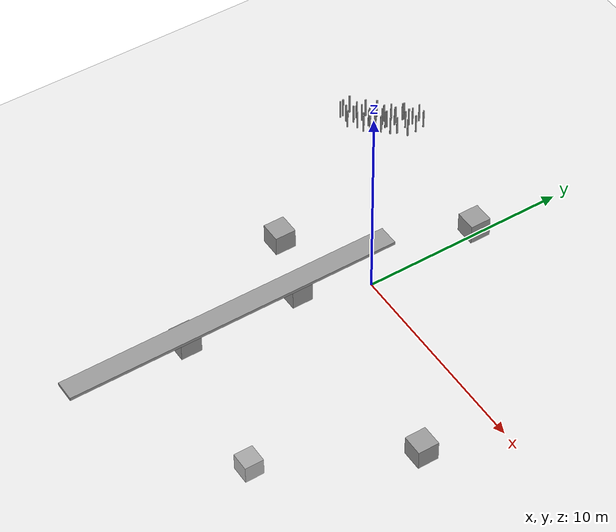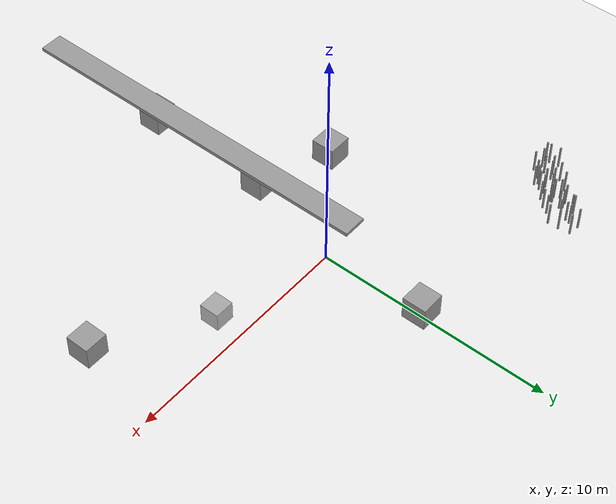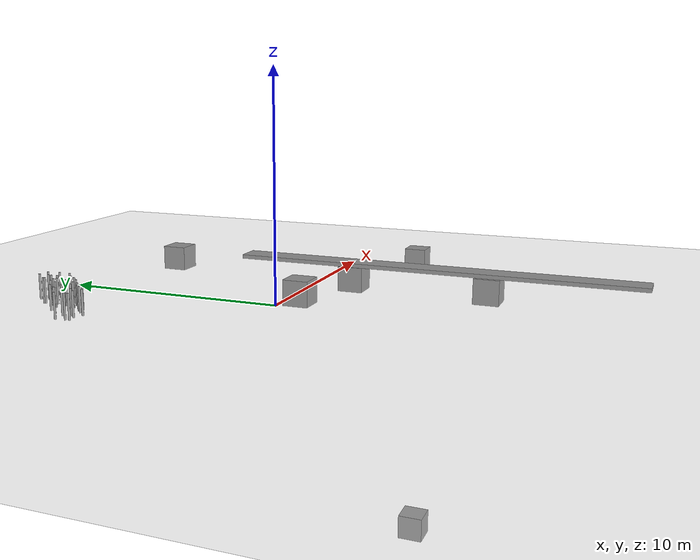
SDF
<sdf version="1.6">
 <world name="default">
  <physics name="default_physics" default="0" type="ode">
   <ode>
    <solver>
     <type>quick</type>
     <iters>20</iters>
     <sor>1</sor>
     <use_dynamic_moi_rescaling>0</use_dynamic_moi_rescaling>
    </solver>
    <constraints>
     <cfm>0</cfm>
     <erp>0.2</erp>
     <contact_max_correcting_vel>100</contact_max_correcting_vel>
     <contact_surface_layer>0</contact_surface_layer>
    </constraints>
   </ode>
   <max_step_size>0.001</max_step_size>
   <real_time_factor>1</real_time_factor>
   <real_time_update_rate>1000</real_time_update_rate>
  </physics>
  <light name="sun" type="directional">
   <pose>0 0 10 0 -0 0</pose>
   <diffuse>0.8 0.8 0.8 1</diffuse>
   <specular>0.2 0.2 0.2 1</specular>
   <attenuation>
    <range>1000</range>
    <constant>0.9</constant>
    <linear>0.01</linear>
    <quadratic>0.001</quadratic>
   </attenuation>
   <direction>-0.5 0.1 -0.9</direction>
  </light>
  <model name="ground_plane">
   <static>1</static>
   <link name="link">
    <collision name="collision">
     <geometry><plane><normal>0 0 1</normal><size>100 100</size></plane></geometry>
     <surface>
      <contact><collide_bitmask>65535</collide_bitmask></contact>
      <friction><ode><mu>100</mu><mu2>50</mu2></ode></friction>
     </surface>
    </collision>
    <visual name="visual">
     <cast_shadows>0</cast_shadows>
     <geometry><plane><normal>0 0 1</normal><size>100 100</size></plane></geometry>
     <material>
      <script><uri>file://media/materials/scripts/gazebo.material</uri><name>Gazebo/Grey</name></script>
     </material>
    </visual>
   </link>
  </model>
  <gravity>0 0 -9.8</gravity>
  <magnetic_field>6e-06 2.3e-05 -4.2e-05</magnetic_field>
  <atmosphere type="adiabatic"/>
  <scene><ambient>0.4 0.4 0.4 1</ambient><background>0.7 0.7 0.7 1</background><shadows>1</shadows></scene>
  <audio><device>default</device></audio>
  <spherical_coordinates>
   <surface_model>EARTH_WGS84</surface_model>
   <latitude_deg>0</latitude_deg>
   <longitude_deg>0</longitude_deg>
   <elevation>0</elevation>
   <heading_deg>0</heading_deg>
  </spherical_coordinates>
  <model name="unit_box">
   <pose>0.686934 4.97774 1.63725 0 -8e-06 -3.1e-05</pose>
   <link name="link">
    <inertial>
     <mass>1</mass>
     <inertia>
      <ixx>0.166667</ixx>
      <ixy>0</ixy>
      <ixz>0</ixz>
      <iyy>0.166667</iyy>
      <iyz>0</iyz>
      <izz>0.166667</izz>
     </inertia>
    </inertial>
    <collision name="collision"><geometry><box><size>1 1 1</size></box></geometry></collision>
    <visual name="visual">
     <geometry><box><size>1 1 1</size></box></geometry>
     <material>
      <script><name>Gazebo/Grey</name><uri>file://media/materials/scripts/gazebo.material</uri></script>
     </material>
    </visual>
   </link>
  </model>
  <model name="unit_cylinder_clone_16">
   <link name="link">
    <inertial>
     <mass>10000.1</mass>
     <inertia><ixx>837.395</ixx><ixy>0</ixy><ixz>0</ixz><iyy>837.395</iyy><iyz>0</iyz><izz>8.09922</izz></inertia>
    </inertial>
    <visual name="visual">
     <geometry><cylinder><radius>0.0402468</radius><length>1</length></cylinder></geometry>
     <material>
      <script><name>Gazebo/Grey</name><uri>file://media/materials/scripts/gazebo.material</uri></script>
      <shader type="vertex"><normal_map>__default__</normal_map></shader>
     </material>
    </visual>
    <collision name="collision">
     <geometry><cylinder><radius>0.040247</radius><length>1</length></cylinder></geometry>
     <surface>
      <friction>
       <ode><mu>1</mu><mu2>1</mu2><fdir1>0 0 0</fdir1><slip1>0</slip1><slip2>0</slip2></ode>
       <torsional>
        <coefficient>1</coefficient>
        <patch_radius>0</patch_radius>
        <surface_radius>0</surface_radius>
        <use_patch_radius>1</use_patch_radius>
        <ode><slip>0</slip></ode>
       </torsional>
      </friction>
      <bounce><restitution_coefficient>0</restitution_coefficient><threshold>1e+06</threshold></bounce>
      <contact>
       <collide_without_contact>0</collide_without_contact>
       <collide_without_contact_bitmask>1</collide_without_contact_bitmask>
       <collide_bitmask>1</collide_bitmask>
       <ode>
        <soft_cfm>0</soft_cfm>
        <soft_erp>0.2</soft_erp>
        <kp>1e+13</kp>
        <kd>1</kd>
        <max_vel>0.01</max_vel>
        <min_depth>0</min_depth>
       </ode>
       <bullet>
        <split_impulse>1</split_impulse>
        <split_impulse_penetration_threshold>-0.01</split_impulse_penetration_threshold>
        <soft_cfm>0</soft_cfm>
        <soft_erp>0.2</soft_erp>
        <kp>1e+13</kp>
        <kd>1</kd>
       </bullet>
      </contact>
     </surface>
    </collision>
   </link>
   <static>0</static>
   <pose>-7.3486 4.45543 1.63725 0 1e-06 -0.000391</pose>
  </model>
  <model name="unit_cylinder_clone_16_clone">
   <link name="link">
    <inertial>
     <mass>10000.1</mass>
     <inertia><ixx>837.395</ixx><ixy>0</ixy><ixz>0</ixz><iyy>837.395</iyy><iyz>0</iyz><izz>8.09922</izz></inertia>
    </inertial>
    <visual name="visual">
     <geometry><cylinder><radius>0.0402468</radius><length>1</length></cylinder></geometry>
     <material>
      <script><name>Gazebo/Grey</name><uri>file://media/materials/scripts/gazebo.material</uri></script>
      <shader type="vertex"><normal_map>__default__</normal_map></shader>
     </material>
    </visual>
    <collision name="collision">
     <geometry><cylinder><radius>0.040247</radius><length>1</length></cylinder></geometry>
     <surface>
      <friction>
       <ode><mu>1</mu><mu2>1</mu2><fdir1>0 0 0</fdir1><slip1>0</slip1><slip2>0</slip2></ode>
       <torsional>
        <coefficient>1</coefficient>
        <patch_radius>0</patch_radius>
        <surface_radius>0</surface_radius>
        <use_patch_radius>1</use_patch_radius>
        <ode><slip>0</slip></ode>
       </torsional>
      </friction>
      <bounce><restitution_coefficient>0</restitution_coefficient><threshold>1e+06</threshold></bounce>
      <contact>
       <collide_without_contact>0</collide_without_contact>
       <collide_without_contact_bitmask>1</collide_without_contact_bitmask>
       <collide_bitmask>1</collide_bitmask>
       <ode>
        <soft_cfm>0</soft_cfm>
        <soft_erp>0.2</soft_erp>
        <kp>1e+13</kp>
        <kd>1</kd>
        <max_vel>0.01</max_vel>
        <min_depth>0</min_depth>
       </ode>
       <bullet>
        <split_impulse>1</split_impulse>
        <split_impulse_penetration_threshold>-0.01</split_impulse_penetration_threshold>
        <soft_cfm>0</soft_cfm>
        <soft_erp>0.2</soft_erp>
        <kp>1e+13</kp>
        <kd>1</kd>
       </bullet>
      </contact>
     </surface>
    </collision>
   </link>
   <static>0</static>
   <pose>-8.77538 4.62833 1.63725 -1e-06 9e-06 -0.000754</pose>
  </model>
  <model name="unit_cylinder_clone_16_clone_0">
   <link name="link">
    <inertial>
     <mass>10000.1</mass>
     <inertia><ixx>837.395</ixx><ixy>0</ixy><ixz>0</ixz><iyy>837.395</iyy><iyz>0</iyz><izz>8.09922</izz></inertia>
    </inertial>
    <visual name="visual">
     <geometry><cylinder><radius>0.0402468</radius><length>1</length></cylinder></geometry>
     <material>
      <script><name>Gazebo/Grey</name><uri>file://media/materials/scripts/gazebo.material</uri></script>
      <shader type="vertex"><normal_map>__default__</normal_map></shader>
     </material>
    </visual>
    <collision name="collision">
     <geometry><cylinder><radius>0.040247</radius><length>1</length></cylinder></geometry>
     <surface>
      <friction>
       <ode><mu>1</mu><mu2>1</mu2><fdir1>0 0 0</fdir1><slip1>0</slip1><slip2>0</slip2></ode>
       <torsional>
        <coefficient>1</coefficient>
        <patch_radius>0</patch_radius>
        <surface_radius>0</surface_radius>
        <use_patch_radius>1</use_patch_radius>
        <ode><slip>0</slip></ode>
       </torsional>
      </friction>
      <bounce><restitution_coefficient>0</restitution_coefficient><threshold>1e+06</threshold></bounce>
      <contact>
       <collide_without_contact>0</collide_without_contact>
       <collide_without_contact_bitmask>1</collide_without_contact_bitmask>
       <collide_bitmask>1</collide_bitmask>
       <ode>
        <soft_cfm>0</soft_cfm>
        <soft_erp>0.2</soft_erp>
        <kp>1e+13</kp>
        <kd>1</kd>
        <max_vel>0.01</max_vel>
        <min_depth>0</min_depth>
       </ode>
       <bullet>
        <split_impulse>1</split_impulse>
        <split_impulse_penetration_threshold>-0.01</split_impulse_penetration_threshold>
        <soft_cfm>0</soft_cfm>
        <soft_erp>0.2</soft_erp>
        <kp>1e+13</kp>
        <kd>1</kd>
       </bullet>
      </contact>
     </surface>
    </collision>
   </link>
   <static>0</static>
   <pose>-8.26675 4.68609 1.63725 -0 -2e-06 -0.000138</pose>
  </model>
  <model name="unit_cylinder_clone_16_clone_1">
   <link name="link">
    <inertial>
     <mass>10000.1</mass>
     <inertia><ixx>837.395</ixx><ixy>0</ixy><ixz>0</ixz><iyy>837.395</iyy><iyz>0</iyz><izz>8.09922</izz></inertia>
    </inertial>
    <visual name="visual">
     <geometry><cylinder><radius>0.0402468</radius><length>1</length></cylinder></geometry>
     <material>
      <script><name>Gazebo/Grey</name><uri>file://media/materials/scripts/gazebo.material</uri></script>
      <shader type="vertex"><normal_map>__default__</normal_map></shader>
     </material>
    </visual>
    <collision name="collision">
     <geometry><cylinder><radius>0.040247</radius><length>1</length></cylinder></geometry>
     <surface>
      <friction>
       <ode><mu>1</mu><mu2>1</mu2><fdir1>0 0 0</fdir1><slip1>0</slip1><slip2>0</slip2></ode>
       <torsional>
        <coefficient>1</coefficient>
        <patch_radius>0</patch_radius>
        <surface_radius>0</surface_radius>
        <use_patch_radius>1</use_patch_radius>
        <ode><slip>0</slip></ode>
       </torsional>
      </friction>
      <bounce><restitution_coefficient>0</restitution_coefficient><threshold>1e+06</threshold></bounce>
      <contact>
       <collide_without_contact>0</collide_without_contact>
       <collide_without_contact_bitmask>1</collide_without_contact_bitmask>
       <collide_bitmask>1</collide_bitmask>
       <ode>
        <soft_cfm>0</soft_cfm>
        <soft_erp>0.2</soft_erp>
        <kp>1e+13</kp>
        <kd>1</kd>
        <max_vel>0.01</max_vel>
        <min_depth>0</min_depth>
       </ode>
       <bullet>
        <split_impulse>1</split_impulse>
        <split_impulse_penetration_threshold>-0.01</split_impulse_penetration_threshold>
        <soft_cfm>0</soft_cfm>
        <soft_erp>0.2</soft_erp>
        <kp>1e+13</kp>
        <kd>1</kd>
       </bullet>
      </contact>
     </surface>
    </collision>
   </link>
   <static>0</static>
   <pose>-7.51513 4.85463 1.63725 0 1e-06 -0.0007</pose>
  </model>
  <model name="unit_cylinder_clone_16_clone_2">
   <link name="link">
    <inertial>
     <mass>10000.1</mass>
     <inertia><ixx>837.395</ixx><ixy>0</ixy><ixz>0</ixz><iyy>837.395</iyy><iyz>0</iyz><izz>8.09922</izz></inertia>
    </inertial>
    <visual name="visual">
     <geometry><cylinder><radius>0.0402468</radius><length>1</length></cylinder></geometry>
     <material>
      <script><name>Gazebo/Grey</name><uri>file://media/materials/scripts/gazebo.material</uri></script>
      <shader type="vertex"><normal_map>__default__</normal_map></shader>
     </material>
    </visual>
    <collision name="collision">
     <geometry><cylinder><radius>0.040247</radius><length>1</length></cylinder></geometry>
     <surface>
      <friction>
       <ode><mu>1</mu><mu2>1</mu2><fdir1>0 0 0</fdir1><slip1>0</slip1><slip2>0</slip2></ode>
       <torsional>
        <coefficient>1</coefficient>
        <patch_radius>0</patch_radius>
        <surface_radius>0</surface_radius>
        <use_patch_radius>1</use_patch_radius>
        <ode><slip>0</slip></ode>
       </torsional>
      </friction>
      <bounce><restitution_coefficient>0</restitution_coefficient><threshold>1e+06</threshold></bounce>
      <contact>
       <collide_without_contact>0</collide_without_contact>
       <collide_without_contact_bitmask>1</collide_without_contact_bitmask>
       <collide_bitmask>1</collide_bitmask>
       <ode>
        <soft_cfm>0</soft_cfm>
        <soft_erp>0.2</soft_erp>
        <kp>1e+13</kp>
        <kd>1</kd>
        <max_vel>0.01</max_vel>
        <min_depth>0</min_depth>
       </ode>
       <bullet>
        <split_impulse>1</split_impulse>
        <split_impulse_penetration_threshold>-0.01</split_impulse_penetration_threshold>
        <soft_cfm>0</soft_cfm>
        <soft_erp>0.2</soft_erp>
        <kp>1e+13</kp>
        <kd>1</kd>
       </bullet>
      </contact>
     </surface>
    </collision>
   </link>
   <static>0</static>
   <pose>-8.15207 5.10482 1.63725 -0 -2e-06 -0.000138</pose>
  </model>
  <model name="unit_cylinder_clone_16_clone_3">
   <link name="link">
    <inertial>
     <mass>10000.1</mass>
     <inertia><ixx>837.395</ixx><ixy>0</ixy><ixz>0</ixz><iyy>837.395</iyy><iyz>0</iyz><izz>8.09922</izz></inertia>
    </inertial>
    <visual name="visual">
     <geometry><cylinder><radius>0.0402468</radius><length>1</length></cylinder></geometry>
     <material>
      <script><name>Gazebo/Grey</name><uri>file://media/materials/scripts/gazebo.material</uri></script>
      <shader type="vertex"><normal_map>__default__</normal_map></shader>
     </material>
    </visual>
    <collision name="collision">
     <geometry><cylinder><radius>0.040247</radius><length>1</length></cylinder></geometry>
     <surface>
      <friction>
       <ode><mu>1</mu><mu2>1</mu2><fdir1>0 0 0</fdir1><slip1>0</slip1><slip2>0</slip2></ode>
       <torsional>
        <coefficient>1</coefficient>
        <patch_radius>0</patch_radius>
        <surface_radius>0</surface_radius>
        <use_patch_radius>1</use_patch_radius>
        <ode><slip>0</slip></ode>
       </torsional>
      </friction>
      <bounce><restitution_coefficient>0</restitution_coefficient><threshold>1e+06</threshold></bounce>
      <contact>
       <collide_without_contact>0</collide_without_contact>
       <collide_without_contact_bitmask>1</collide_without_contact_bitmask>
       <collide_bitmask>1</collide_bitmask>
       <ode>
        <soft_cfm>0</soft_cfm>
        <soft_erp>0.2</soft_erp>
        <kp>1e+13</kp>
        <kd>1</kd>
        <max_vel>0.01</max_vel>
        <min_depth>0</min_depth>
       </ode>
       <bullet>
        <split_impulse>1</split_impulse>
        <split_impulse_penetration_threshold>-0.01</split_impulse_penetration_threshold>
        <soft_cfm>0</soft_cfm>
        <soft_erp>0.2</soft_erp>
        <kp>1e+13</kp>
        <kd>1</kd>
       </bullet>
      </contact>
     </surface>
    </collision>
   </link>
   <static>0</static>
   <pose>-7.75658 5.07348 1.63725 -0 2e-06 -0.000198</pose>
  </model>
  <model name="unit_cylinder_clone_16_clone_4">
   <link name="link">
    <inertial>
     <mass>10000.1</mass>
     <inertia><ixx>837.395</ixx><ixy>0</ixy><ixz>0</ixz><iyy>837.395</iyy><iyz>0</iyz><izz>8.09922</izz></inertia>
    </inertial>
    <visual name="visual">
     <geometry><cylinder><radius>0.0402468</radius><length>1</length></cylinder></geometry>
     <material>
      <script><name>Gazebo/Grey</name><uri>file://media/materials/scripts/gazebo.material</uri></script>
      <shader type="vertex"><normal_map>__default__</normal_map></shader>
     </material>
    </visual>
    <collision name="collision">
     <geometry><cylinder><radius>0.040247</radius><length>1</length></cylinder></geometry>
     <surface>
      <friction>
       <ode><mu>1</mu><mu2>1</mu2><fdir1>0 0 0</fdir1><slip1>0</slip1><slip2>0</slip2></ode>
       <torsional>
        <coefficient>1</coefficient>
        <patch_radius>0</patch_radius>
        <surface_radius>0</surface_radius>
        <use_patch_radius>1</use_patch_radius>
        <ode><slip>0</slip></ode>
       </torsional>
      </friction>
      <bounce><restitution_coefficient>0</restitution_coefficient><threshold>1e+06</threshold></bounce>
      <contact>
       <collide_without_contact>0</collide_without_contact>
       <collide_without_contact_bitmask>1</collide_without_contact_bitmask>
       <collide_bitmask>1</collide_bitmask>
       <ode>
        <soft_cfm>0</soft_cfm>
        <soft_erp>0.2</soft_erp>
        <kp>1e+13</kp>
        <kd>1</kd>
        <max_vel>0.01</max_vel>
        <min_depth>0</min_depth>
       </ode>
       <bullet>
        <split_impulse>1</split_impulse>
        <split_impulse_penetration_threshold>-0.01</split_impulse_penetration_threshold>
        <soft_cfm>0</soft_cfm>
        <soft_erp>0.2</soft_erp>
        <kp>1e+13</kp>
        <kd>1</kd>
       </bullet>
      </contact>
     </surface>
    </collision>
   </link>
   <static>0</static>
   <pose>-7.99203 4.79193 1.63725 1e-06 -1e-06 -0.000676</pose>
  </model>
  <model name="unit_cylinder_clone_16_clone_5">
   <link name="link">
    <inertial>
     <mass>10000.1</mass>
     <inertia><ixx>837.395</ixx><ixy>0</ixy><ixz>0</ixz><iyy>837.395</iyy><iyz>0</iyz><izz>8.09922</izz></inertia>
    </inertial>
    <visual name="visual">
     <geometry><cylinder><radius>0.0402468</radius><length>1</length></cylinder></geometry>
     <material>
      <script><name>Gazebo/Grey</name><uri>file://media/materials/scripts/gazebo.material</uri></script>
      <shader type="vertex"><normal_map>__default__</normal_map></shader>
     </material>
    </visual>
    <collision name="collision">
     <geometry><cylinder><radius>0.040247</radius><length>1</length></cylinder></geometry>
     <surface>
      <friction>
       <ode><mu>1</mu><mu2>1</mu2><fdir1>0 0 0</fdir1><slip1>0</slip1><slip2>0</slip2></ode>
       <torsional>
        <coefficient>1</coefficient>
        <patch_radius>0</patch_radius>
        <surface_radius>0</surface_radius>
        <use_patch_radius>1</use_patch_radius>
        <ode><slip>0</slip></ode>
       </torsional>
      </friction>
      <bounce><restitution_coefficient>0</restitution_coefficient><threshold>1e+06</threshold></bounce>
      <contact>
       <collide_without_contact>0</collide_without_contact>
       <collide_without_contact_bitmask>1</collide_without_contact_bitmask>
       <collide_bitmask>1</collide_bitmask>
       <ode>
        <soft_cfm>0</soft_cfm>
        <soft_erp>0.2</soft_erp>
        <kp>1e+13</kp>
        <kd>1</kd>
        <max_vel>0.01</max_vel>
        <min_depth>0</min_depth>
       </ode>
       <bullet>
        <split_impulse>1</split_impulse>
        <split_impulse_penetration_threshold>-0.01</split_impulse_penetration_threshold>
        <soft_cfm>0</soft_cfm>
        <soft_erp>0.2</soft_erp>
        <kp>1e+13</kp>
        <kd>1</kd>
       </bullet>
      </contact>
     </surface>
    </collision>
   </link>
   <static>0</static>
   <pose>-7.48047 4.54281 1.63725 -1e-06 1e-06 -0.000569</pose>
  </model>
  <model name="unit_cylinder_clone_16_clone_6">
   <link name="link">
    <inertial>
     <mass>10000.1</mass>
     <inertia><ixx>837.395</ixx><ixy>0</ixy><ixz>0</ixz><iyy>837.395</iyy><iyz>0</iyz><izz>8.09922</izz></inertia>
    </inertial>
    <visual name="visual">
     <geometry><cylinder><radius>0.0402468</radius><length>1</length></cylinder></geometry>
     <material>
      <script><name>Gazebo/Grey</name><uri>file://media/materials/scripts/gazebo.material</uri></script>
      <shader type="vertex"><normal_map>__default__</normal_map></shader>
     </material>
    </visual>
    <collision name="collision">
     <geometry><cylinder><radius>0.040247</radius><length>1</length></cylinder></geometry>
     <surface>
      <friction>
       <ode><mu>1</mu><mu2>1</mu2><fdir1>0 0 0</fdir1><slip1>0</slip1><slip2>0</slip2></ode>
       <torsional>
        <coefficient>1</coefficient>
        <patch_radius>0</patch_radius>
        <surface_radius>0</surface_radius>
        <use_patch_radius>1</use_patch_radius>
        <ode><slip>0</slip></ode>
       </torsional>
      </friction>
      <bounce><restitution_coefficient>0</restitution_coefficient><threshold>1e+06</threshold></bounce>
      <contact>
       <collide_without_contact>0</collide_without_contact>
       <collide_without_contact_bitmask>1</collide_without_contact_bitmask>
       <collide_bitmask>1</collide_bitmask>
       <ode>
        <soft_cfm>0</soft_cfm>
        <soft_erp>0.2</soft_erp>
        <kp>1e+13</kp>
        <kd>1</kd>
        <max_vel>0.01</max_vel>
        <min_depth>0</min_depth>
       </ode>
       <bullet>
        <split_impulse>1</split_impulse>
        <split_impulse_penetration_threshold>-0.01</split_impulse_penetration_threshold>
        <soft_cfm>0</soft_cfm>
        <soft_erp>0.2</soft_erp>
        <kp>1e+13</kp>
        <kd>1</kd>
       </bullet>
      </contact>
     </surface>
    </collision>
   </link>
   <static>0</static>
   <pose>-8.10977 4.40716 1.63725 -1e-06 -0 -0.000336</pose>
  </model>
  <model name="unit_cylinder_clone_16_clone_7">
   <link name="link">
    <inertial>
     <mass>10000.1</mass>
     <inertia><ixx>837.395</ixx><ixy>0</ixy><ixz>0</ixz><iyy>837.395</iyy><iyz>0</iyz><izz>8.09922</izz></inertia>
    </inertial>
    <visual name="visual">
     <geometry><cylinder><radius>0.0402468</radius><length>1</length></cylinder></geometry>
     <material>
      <script><name>Gazebo/Grey</name><uri>file://media/materials/scripts/gazebo.material</uri></script>
      <shader type="vertex"><normal_map>__default__</normal_map></shader>
     </material>
    </visual>
    <collision name="collision">
     <geometry><cylinder><radius>0.040247</radius><length>1</length></cylinder></geometry>
     <surface>
      <friction>
       <ode><mu>1</mu><mu2>1</mu2><fdir1>0 0 0</fdir1><slip1>0</slip1><slip2>0</slip2></ode>
       <torsional>
        <coefficient>1</coefficient>
        <patch_radius>0</patch_radius>
        <surface_radius>0</surface_radius>
        <use_patch_radius>1</use_patch_radius>
        <ode><slip>0</slip></ode>
       </torsional>
      </friction>
      <bounce><restitution_coefficient>0</restitution_coefficient><threshold>1e+06</threshold></bounce>
      <contact>
       <collide_without_contact>0</collide_without_contact>
       <collide_without_contact_bitmask>1</collide_without_contact_bitmask>
       <collide_bitmask>1</collide_bitmask>
       <ode>
        <soft_cfm>0</soft_cfm>
        <soft_erp>0.2</soft_erp>
        <kp>1e+13</kp>
        <kd>1</kd>
        <max_vel>0.01</max_vel>
        <min_depth>0</min_depth>
       </ode>
       <bullet>
        <split_impulse>1</split_impulse>
        <split_impulse_penetration_threshold>-0.01</split_impulse_penetration_threshold>
        <soft_cfm>0</soft_cfm>
        <soft_erp>0.2</soft_erp>
        <kp>1e+13</kp>
        <kd>1</kd>
       </bullet>
      </contact>
     </surface>
    </collision>
   </link>
   <static>0</static>
   <pose>-7.68692 4.33819 1.63725 1e-06 2e-06 -0.000576</pose>
  </model>
  <model name="unit_cylinder_clone_16_clone_8">
   <link name="link">
    <inertial>
     <mass>10000.1</mass>
     <inertia><ixx>837.395</ixx><ixy>0</ixy><ixz>0</ixz><iyy>837.395</iyy><iyz>0</iyz><izz>8.09922</izz></inertia>
    </inertial>
    <visual name="visual">
     <geometry><cylinder><radius>0.0402468</radius><length>1</length></cylinder></geometry>
     <material>
      <script><name>Gazebo/Grey</name><uri>file://media/materials/scripts/gazebo.material</uri></script>
      <shader type="vertex"><normal_map>__default__</normal_map></shader>
     </material>
    </visual>
    <collision name="collision">
     <geometry><cylinder><radius>0.040247</radius><length>1</length></cylinder></geometry>
     <surface>
      <friction>
       <ode><mu>1</mu><mu2>1</mu2><fdir1>0 0 0</fdir1><slip1>0</slip1><slip2>0</slip2></ode>
       <torsional>
        <coefficient>1</coefficient>
        <patch_radius>0</patch_radius>
        <surface_radius>0</surface_radius>
        <use_patch_radius>1</use_patch_radius>
        <ode><slip>0</slip></ode>
       </torsional>
      </friction>
      <bounce><restitution_coefficient>0</restitution_coefficient><threshold>1e+06</threshold></bounce>
      <contact>
       <collide_without_contact>0</collide_without_contact>
       <collide_without_contact_bitmask>1</collide_without_contact_bitmask>
       <collide_bitmask>1</collide_bitmask>
       <ode>
        <soft_cfm>0</soft_cfm>
        <soft_erp>0.2</soft_erp>
        <kp>1e+13</kp>
        <kd>1</kd>
        <max_vel>0.01</max_vel>
        <min_depth>0</min_depth>
       </ode>
       <bullet>
        <split_impulse>1</split_impulse>
        <split_impulse_penetration_threshold>-0.01</split_impulse_penetration_threshold>
        <soft_cfm>0</soft_cfm>
        <soft_erp>0.2</soft_erp>
        <kp>1e+13</kp>
        <kd>1</kd>
       </bullet>
      </contact>
     </surface>
    </collision>
   </link>
   <static>0</static>
   <pose>-8 4 1.63725 1e-06 -1e-06 -0.000778</pose>
  </model>
  <model name="unit_cylinder_clone_16_clone_9">
   <link name="link">
    <inertial>
     <mass>10000.1</mass>
     <inertia><ixx>837.395</ixx><ixy>0</ixy><ixz>0</ixz><iyy>837.395</iyy><iyz>0</iyz><izz>8.09922</izz></inertia>
    </inertial>
    <visual name="visual">
     <geometry><cylinder><radius>0.0402468</radius><length>1</length></cylinder></geometry>
     <material>
      <script><name>Gazebo/Grey</name><uri>file://media/materials/scripts/gazebo.material</uri></script>
      <shader type="vertex"><normal_map>__default__</normal_map></shader>
     </material>
    </visual>
    <collision name="collision">
     <geometry><cylinder><radius>0.040247</radius><length>1</length></cylinder></geometry>
     <surface>
      <friction>
       <ode><mu>1</mu><mu2>1</mu2><fdir1>0 0 0</fdir1><slip1>0</slip1><slip2>0</slip2></ode>
       <torsional>
        <coefficient>1</coefficient>
        <patch_radius>0</patch_radius>
        <surface_radius>0</surface_radius>
        <use_patch_radius>1</use_patch_radius>
        <ode><slip>0</slip></ode>
       </torsional>
      </friction>
      <bounce><restitution_coefficient>0</restitution_coefficient><threshold>1e+06</threshold></bounce>
      <contact>
       <collide_without_contact>0</collide_without_contact>
       <collide_without_contact_bitmask>1</collide_without_contact_bitmask>
       <collide_bitmask>1</collide_bitmask>
       <ode>
        <soft_cfm>0</soft_cfm>
        <soft_erp>0.2</soft_erp>
        <kp>1e+13</kp>
        <kd>1</kd>
        <max_vel>0.01</max_vel>
        <min_depth>0</min_depth>
       </ode>
       <bullet>
        <split_impulse>1</split_impulse>
        <split_impulse_penetration_threshold>-0.01</split_impulse_penetration_threshold>
        <soft_cfm>0</soft_cfm>
        <soft_erp>0.2</soft_erp>
        <kp>1e+13</kp>
        <kd>1</kd>
       </bullet>
      </contact>
     </surface>
    </collision>
   </link>
   <static>0</static>
   <pose>-8.70341 4.07412 1.63725 -1e-06 -0 -0.000336</pose>
  </model>
  <model name="unit_cylinder_clone_16_clone_10">
   <link name="link">
    <inertial>
     <mass>10000.1</mass>
     <inertia><ixx>837.395</ixx><ixy>0</ixy><ixz>0</ixz><iyy>837.395</iyy><iyz>0</iyz><izz>8.09922</izz></inertia>
    </inertial>
    <visual name="visual">
     <geometry><cylinder><radius>0.0402468</radius><length>1</length></cylinder></geometry>
     <material>
      <script><name>Gazebo/Grey</name><uri>file://media/materials/scripts/gazebo.material</uri></script>
      <shader type="vertex"><normal_map>__default__</normal_map></shader>
     </material>
    </visual>
    <collision name="collision">
     <geometry><cylinder><radius>0.040247</radius><length>1</length></cylinder></geometry>
     <surface>
      <friction>
       <ode><mu>1</mu><mu2>1</mu2><fdir1>0 0 0</fdir1><slip1>0</slip1><slip2>0</slip2></ode>
       <torsional>
        <coefficient>1</coefficient>
        <patch_radius>0</patch_radius>
        <surface_radius>0</surface_radius>
        <use_patch_radius>1</use_patch_radius>
        <ode><slip>0</slip></ode>
       </torsional>
      </friction>
      <bounce><restitution_coefficient>0</restitution_coefficient><threshold>1e+06</threshold></bounce>
      <contact>
       <collide_without_contact>0</collide_without_contact>
       <collide_without_contact_bitmask>1</collide_without_contact_bitmask>
       <collide_bitmask>1</collide_bitmask>
       <ode>
        <soft_cfm>0</soft_cfm>
        <soft_erp>0.2</soft_erp>
        <kp>1e+13</kp>
        <kd>1</kd>
        <max_vel>0.01</max_vel>
        <min_depth>0</min_depth>
       </ode>
       <bullet>
        <split_impulse>1</split_impulse>
        <split_impulse_penetration_threshold>-0.01</split_impulse_penetration_threshold>
        <soft_cfm>0</soft_cfm>
        <soft_erp>0.2</soft_erp>
        <kp>1e+13</kp>
        <kd>1</kd>
       </bullet>
      </contact>
     </surface>
    </collision>
   </link>
   <static>0</static>
   <pose>-8.72926 4.2303 1.63725 0 1e-06 -0.000705</pose>
  </model>
  <model name="unit_cylinder_clone_16_clone_11">
   <link name="link">
    <inertial>
     <mass>10000.1</mass>
     <inertia><ixx>837.395</ixx><ixy>0</ixy><ixz>0</ixz><iyy>837.395</iyy><iyz>0</iyz><izz>8.09922</izz></inertia>
    </inertial>
    <visual name="visual">
     <geometry><cylinder><radius>0.0402468</radius><length>1</length></cylinder></geometry>
     <material>
      <script><name>Gazebo/Grey</name><uri>file://media/materials/scripts/gazebo.material</uri></script>
      <shader type="vertex"><normal_map>__default__</normal_map></shader>
     </material>
    </visual>
    <collision name="collision">
     <geometry><cylinder><radius>0.040247</radius><length>1</length></cylinder></geometry>
     <surface>
      <friction>
       <ode><mu>1</mu><mu2>1</mu2><fdir1>0 0 0</fdir1><slip1>0</slip1><slip2>0</slip2></ode>
       <torsional>
        <coefficient>1</coefficient>
        <patch_radius>0</patch_radius>
        <surface_radius>0</surface_radius>
        <use_patch_radius>1</use_patch_radius>
        <ode><slip>0</slip></ode>
       </torsional>
      </friction>
      <bounce><restitution_coefficient>0</restitution_coefficient><threshold>1e+06</threshold></bounce>
      <contact>
       <collide_without_contact>0</collide_without_contact>
       <collide_without_contact_bitmask>1</collide_without_contact_bitmask>
       <collide_bitmask>1</collide_bitmask>
       <ode>
        <soft_cfm>0</soft_cfm>
        <soft_erp>0.2</soft_erp>
        <kp>1e+13</kp>
        <kd>1</kd>
        <max_vel>0.01</max_vel>
        <min_depth>0</min_depth>
       </ode>
       <bullet>
        <split_impulse>1</split_impulse>
        <split_impulse_penetration_threshold>-0.01</split_impulse_penetration_threshold>
        <soft_cfm>0</soft_cfm>
        <soft_erp>0.2</soft_erp>
        <kp>1e+13</kp>
        <kd>1</kd>
       </bullet>
      </contact>
     </surface>
    </collision>
   </link>
   <static>0</static>
   <pose>-8.34782 4.15429 1.63725 -1e-06 -0 -0.000503</pose>
  </model>
  <model name="unit_cylinder_clone_16_clone_12">
   <link name="link">
    <inertial>
     <mass>10000.1</mass>
     <inertia><ixx>837.395</ixx><ixy>0</ixy><ixz>0</ixz><iyy>837.395</iyy><iyz>0</iyz><izz>8.09922</izz></inertia>
    </inertial>
    <visual name="visual">
     <geometry><cylinder><radius>0.0402468</radius><length>1</length></cylinder></geometry>
     <material>
      <script><name>Gazebo/Grey</name><uri>file://media/materials/scripts/gazebo.material</uri></script>
      <shader type="vertex"><normal_map>__default__</normal_map></shader>
     </material>
    </visual>
    <collision name="collision">
     <geometry><cylinder><radius>0.040247</radius><length>1</length></cylinder></geometry>
     <surface>
      <friction>
       <ode><mu>1</mu><mu2>1</mu2><fdir1>0 0 0</fdir1><slip1>0</slip1><slip2>0</slip2></ode>
       <torsional>
        <coefficient>1</coefficient>
        <patch_radius>0</patch_radius>
        <surface_radius>0</surface_radius>
        <use_patch_radius>1</use_patch_radius>
        <ode><slip>0</slip></ode>
       </torsional>
      </friction>
      <bounce><restitution_coefficient>0</restitution_coefficient><threshold>1e+06</threshold></bounce>
      <contact>
       <collide_without_contact>0</collide_without_contact>
       <collide_without_contact_bitmask>1</collide_without_contact_bitmask>
       <collide_bitmask>1</collide_bitmask>
       <ode>
        <soft_cfm>0</soft_cfm>
        <soft_erp>0.2</soft_erp>
        <kp>1e+13</kp>
        <kd>1</kd>
        <max_vel>0.01</max_vel>
        <min_depth>0</min_depth>
       </ode>
       <bullet>
        <split_impulse>1</split_impulse>
        <split_impulse_penetration_threshold>-0.01</split_impulse_penetration_threshold>
        <soft_cfm>0</soft_cfm>
        <soft_erp>0.2</soft_erp>
        <kp>1e+13</kp>
        <kd>1</kd>
       </bullet>
      </contact>
     </surface>
    </collision>
   </link>
   <static>0</static>
   <pose>-7.24783 4.7443 1.63725 -1e-06 1e-06 -0.000569</pose>
  </model>
  <model name="unit_cylinder_clone_16_clone_13">
   <link name="link">
    <inertial>
     <mass>10000.1</mass>
     <inertia><ixx>837.395</ixx><ixy>0</ixy><ixz>0</ixz><iyy>837.395</iyy><iyz>0</iyz><izz>8.09922</izz></inertia>
    </inertial>
    <visual name="visual">
     <geometry><cylinder><radius>0.0402468</radius><length>1</length></cylinder></geometry>
     <material>
      <script><name>Gazebo/Grey</name><uri>file://media/materials/scripts/gazebo.material</uri></script>
      <shader type="vertex"><normal_map>__default__</normal_map></shader>
     </material>
    </visual>
    <collision name="collision">
     <geometry><cylinder><radius>0.040247</radius><length>1</length></cylinder></geometry>
     <surface>
      <friction>
       <ode><mu>1</mu><mu2>1</mu2><fdir1>0 0 0</fdir1><slip1>0</slip1><slip2>0</slip2></ode>
       <torsional>
        <coefficient>1</coefficient>
        <patch_radius>0</patch_radius>
        <surface_radius>0</surface_radius>
        <use_patch_radius>1</use_patch_radius>
        <ode><slip>0</slip></ode>
       </torsional>
      </friction>
      <bounce><restitution_coefficient>0</restitution_coefficient><threshold>1e+06</threshold></bounce>
      <contact>
       <collide_without_contact>0</collide_without_contact>
       <collide_without_contact_bitmask>1</collide_without_contact_bitmask>
       <collide_bitmask>1</collide_bitmask>
       <ode>
        <soft_cfm>0</soft_cfm>
        <soft_erp>0.2</soft_erp>
        <kp>1e+13</kp>
        <kd>1</kd>
        <max_vel>0.01</max_vel>
        <min_depth>0</min_depth>
       </ode>
       <bullet>
        <split_impulse>1</split_impulse>
        <split_impulse_penetration_threshold>-0.01</split_impulse_penetration_threshold>
        <soft_cfm>0</soft_cfm>
        <soft_erp>0.2</soft_erp>
        <kp>1e+13</kp>
        <kd>1</kd>
       </bullet>
      </contact>
     </surface>
    </collision>
   </link>
   <static>0</static>
   <pose>-7.4541 5.19396 1.63725 5e-06 3e-06 -0.000687</pose>
  </model>
  <model name="unit_cylinder_clone_16_clone_14">
   <link name="link">
    <inertial>
     <mass>10000.1</mass>
     <inertia><ixx>837.395</ixx><ixy>0</ixy><ixz>0</ixz><iyy>837.395</iyy><iyz>0</iyz><izz>8.09922</izz></inertia>
    </inertial>
    <visual name="visual">
     <geometry><cylinder><radius>0.0402468</radius><length>1</length></cylinder></geometry>
     <material>
      <script><name>Gazebo/Grey</name><uri>file://media/materials/scripts/gazebo.material</uri></script>
      <shader type="vertex"><normal_map>__default__</normal_map></shader>
     </material>
    </visual>
    <collision name="collision">
     <geometry><cylinder><radius>0.040247</radius><length>1</length></cylinder></geometry>
     <surface>
      <friction>
       <ode><mu>1</mu><mu2>1</mu2><fdir1>0 0 0</fdir1><slip1>0</slip1><slip2>0</slip2></ode>
       <torsional>
        <coefficient>1</coefficient>
        <patch_radius>0</patch_radius>
        <surface_radius>0</surface_radius>
        <use_patch_radius>1</use_patch_radius>
        <ode><slip>0</slip></ode>
       </torsional>
      </friction>
      <bounce><restitution_coefficient>0</restitution_coefficient><threshold>1e+06</threshold></bounce>
      <contact>
       <collide_without_contact>0</collide_without_contact>
       <collide_without_contact_bitmask>1</collide_without_contact_bitmask>
       <collide_bitmask>1</collide_bitmask>
       <ode>
        <soft_cfm>0</soft_cfm>
        <soft_erp>0.2</soft_erp>
        <kp>1e+13</kp>
        <kd>1</kd>
        <max_vel>0.01</max_vel>
        <min_depth>0</min_depth>
       </ode>
       <bullet>
        <split_impulse>1</split_impulse>
        <split_impulse_penetration_threshold>-0.01</split_impulse_penetration_threshold>
        <soft_cfm>0</soft_cfm>
        <soft_erp>0.2</soft_erp>
        <kp>1e+13</kp>
        <kd>1</kd>
       </bullet>
      </contact>
     </surface>
    </collision>
   </link>
   <static>0</static>
   <pose>-7.83085 5.5223 1.63725 -1e-06 -0 -0.000583</pose>
  </model>
  <model name="unit_cylinder_clone_16_clone_15">
   <link name="link">
    <inertial>
     <mass>10000.1</mass>
     <inertia><ixx>837.395</ixx><ixy>0</ixy><ixz>0</ixz><iyy>837.395</iyy><iyz>0</iyz><izz>8.09922</izz></inertia>
    </inertial>
    <visual name="visual">
     <geometry><cylinder><radius>0.0402468</radius><length>1</length></cylinder></geometry>
     <material>
      <script><name>Gazebo/Grey</name><uri>file://media/materials/scripts/gazebo.material</uri></script>
      <shader type="vertex"><normal_map>__default__</normal_map></shader>
     </material>
    </visual>
    <collision name="collision">
     <geometry><cylinder><radius>0.040247</radius><length>1</length></cylinder></geometry>
     <surface>
      <friction>
       <ode><mu>1</mu><mu2>1</mu2><fdir1>0 0 0</fdir1><slip1>0</slip1><slip2>0</slip2></ode>
       <torsional>
        <coefficient>1</coefficient>
        <patch_radius>0</patch_radius>
        <surface_radius>0</surface_radius>
        <use_patch_radius>1</use_patch_radius>
        <ode><slip>0</slip></ode>
       </torsional>
      </friction>
      <bounce><restitution_coefficient>0</restitution_coefficient><threshold>1e+06</threshold></bounce>
      <contact>
       <collide_without_contact>0</collide_without_contact>
       <collide_without_contact_bitmask>1</collide_without_contact_bitmask>
       <collide_bitmask>1</collide_bitmask>
       <ode>
        <soft_cfm>0</soft_cfm>
        <soft_erp>0.2</soft_erp>
        <kp>1e+13</kp>
        <kd>1</kd>
        <max_vel>0.01</max_vel>
        <min_depth>0</min_depth>
       </ode>
       <bullet>
        <split_impulse>1</split_impulse>
        <split_impulse_penetration_threshold>-0.01</split_impulse_penetration_threshold>
        <soft_cfm>0</soft_cfm>
        <soft_erp>0.2</soft_erp>
        <kp>1e+13</kp>
        <kd>1</kd>
       </bullet>
      </contact>
     </surface>
    </collision>
   </link>
   <static>0</static>
   <pose>-7.00003 5.51305 1.63725 0 -1e-06 0.001204</pose>
  </model>
  <model name="unit_cylinder_clone_16_clone_16">
   <link name="link">
    <inertial>
     <mass>10000.1</mass>
     <inertia><ixx>837.395</ixx><ixy>0</ixy><ixz>0</ixz><iyy>837.395</iyy><iyz>0</iyz><izz>8.09922</izz></inertia>
    </inertial>
    <visual name="visual">
     <geometry><cylinder><radius>0.0402468</radius><length>1</length></cylinder></geometry>
     <material>
      <script><name>Gazebo/Grey</name><uri>file://media/materials/scripts/gazebo.material</uri></script>
      <shader type="vertex"><normal_map>__default__</normal_map></shader>
     </material>
    </visual>
    <collision name="collision">
     <geometry><cylinder><radius>0.040247</radius><length>1</length></cylinder></geometry>
     <surface>
      <friction>
       <ode><mu>1</mu><mu2>1</mu2><fdir1>0 0 0</fdir1><slip1>0</slip1><slip2>0</slip2></ode>
       <torsional>
        <coefficient>1</coefficient>
        <patch_radius>0</patch_radius>
        <surface_radius>0</surface_radius>
        <use_patch_radius>1</use_patch_radius>
        <ode><slip>0</slip></ode>
       </torsional>
      </friction>
      <bounce><restitution_coefficient>0</restitution_coefficient><threshold>1e+06</threshold></bounce>
      <contact>
       <collide_without_contact>0</collide_without_contact>
       <collide_without_contact_bitmask>1</collide_without_contact_bitmask>
       <collide_bitmask>1</collide_bitmask>
       <ode>
        <soft_cfm>0</soft_cfm>
        <soft_erp>0.2</soft_erp>
        <kp>1e+13</kp>
        <kd>1</kd>
        <max_vel>0.01</max_vel>
        <min_depth>0</min_depth>
       </ode>
       <bullet>
        <split_impulse>1</split_impulse>
        <split_impulse_penetration_threshold>-0.01</split_impulse_penetration_threshold>
        <soft_cfm>0</soft_cfm>
        <soft_erp>0.2</soft_erp>
        <kp>1e+13</kp>
        <kd>1</kd>
       </bullet>
      </contact>
     </surface>
    </collision>
   </link>
   <static>0</static>
   <pose>-7.18955 4.98049 1.63725 0 1e-06 -0.0007</pose>
  </model>
  <model name="unit_cylinder_clone_16_clone_17">
   <link name="link">
    <inertial>
     <mass>10000.1</mass>
     <inertia><ixx>837.395</ixx><ixy>0</ixy><ixz>0</ixz><iyy>837.395</iyy><iyz>0</iyz><izz>8.09922</izz></inertia>
    </inertial>
    <visual name="visual">
     <geometry><cylinder><radius>0.0402468</radius><length>1</length></cylinder></geometry>
     <material>
      <script><name>Gazebo/Grey</name><uri>file://media/materials/scripts/gazebo.material</uri></script>
      <shader type="vertex"><normal_map>__default__</normal_map></shader>
     </material>
    </visual>
    <collision name="collision">
     <geometry><cylinder><radius>0.040247</radius><length>1</length></cylinder></geometry>
     <surface>
      <friction>
       <ode><mu>1</mu><mu2>1</mu2><fdir1>0 0 0</fdir1><slip1>0</slip1><slip2>0</slip2></ode>
       <torsional>
        <coefficient>1</coefficient>
        <patch_radius>0</patch_radius>
        <surface_radius>0</surface_radius>
        <use_patch_radius>1</use_patch_radius>
        <ode><slip>0</slip></ode>
       </torsional>
      </friction>
      <bounce><restitution_coefficient>0</restitution_coefficient><threshold>1e+06</threshold></bounce>
      <contact>
       <collide_without_contact>0</collide_without_contact>
       <collide_without_contact_bitmask>1</collide_without_contact_bitmask>
       <collide_bitmask>1</collide_bitmask>
       <ode>
        <soft_cfm>0</soft_cfm>
        <soft_erp>0.2</soft_erp>
        <kp>1e+13</kp>
        <kd>1</kd>
        <max_vel>0.01</max_vel>
        <min_depth>0</min_depth>
       </ode>
       <bullet>
        <split_impulse>1</split_impulse>
        <split_impulse_penetration_threshold>-0.01</split_impulse_penetration_threshold>
        <soft_cfm>0</soft_cfm>
        <soft_erp>0.2</soft_erp>
        <kp>1e+13</kp>
        <kd>1</kd>
       </bullet>
      </contact>
     </surface>
    </collision>
   </link>
   <static>0</static>
   <pose>-7.24714 5.42523 1.63725 -1e-06 1e-06 -0.000569</pose>
  </model>
  <model name="unit_cylinder_clone_16_clone_18">
   <link name="link">
    <inertial>
     <mass>10000.1</mass>
     <inertia><ixx>837.395</ixx><ixy>0</ixy><ixz>0</ixz><iyy>837.395</iyy><iyz>0</iyz><izz>8.09922</izz></inertia>
    </inertial>
    <visual name="visual">
     <geometry><cylinder><radius>0.0402468</radius><length>1</length></cylinder></geometry>
     <material>
      <script><name>Gazebo/Grey</name><uri>file://media/materials/scripts/gazebo.material</uri></script>
      <shader type="vertex"><normal_map>__default__</normal_map></shader>
     </material>
    </visual>
    <collision name="collision">
     <geometry><cylinder><radius>0.040247</radius><length>1</length></cylinder></geometry>
     <surface>
      <friction>
       <ode><mu>1</mu><mu2>1</mu2><fdir1>0 0 0</fdir1><slip1>0</slip1><slip2>0</slip2></ode>
       <torsional>
        <coefficient>1</coefficient>
        <patch_radius>0</patch_radius>
        <surface_radius>0</surface_radius>
        <use_patch_radius>1</use_patch_radius>
        <ode><slip>0</slip></ode>
       </torsional>
      </friction>
      <bounce><restitution_coefficient>0</restitution_coefficient><threshold>1e+06</threshold></bounce>
      <contact>
       <collide_without_contact>0</collide_without_contact>
       <collide_without_contact_bitmask>1</collide_without_contact_bitmask>
       <collide_bitmask>1</collide_bitmask>
       <ode>
        <soft_cfm>0</soft_cfm>
        <soft_erp>0.2</soft_erp>
        <kp>1e+13</kp>
        <kd>1</kd>
        <max_vel>0.01</max_vel>
        <min_depth>0</min_depth>
       </ode>
       <bullet>
        <split_impulse>1</split_impulse>
        <split_impulse_penetration_threshold>-0.01</split_impulse_penetration_threshold>
        <soft_cfm>0</soft_cfm>
        <soft_erp>0.2</soft_erp>
        <kp>1e+13</kp>
        <kd>1</kd>
       </bullet>
      </contact>
     </surface>
    </collision>
   </link>
   <static>0</static>
   <pose>-7.39391 5.627 1.63725 -1e-06 -0 -0.000486</pose>
  </model>
  <model name="unit_cylinder_clone_16_clone_19">
   <link name="link">
    <inertial>
     <mass>10000.1</mass>
     <inertia><ixx>837.395</ixx><ixy>0</ixy><ixz>0</ixz><iyy>837.395</iyy><iyz>0</iyz><izz>8.09922</izz></inertia>
    </inertial>
    <visual name="visual">
     <geometry><cylinder><radius>0.0402468</radius><length>1</length></cylinder></geometry>
     <material>
      <script><name>Gazebo/Grey</name><uri>file://media/materials/scripts/gazebo.material</uri></script>
      <shader type="vertex"><normal_map>__default__</normal_map></shader>
     </material>
    </visual>
    <collision name="collision">
     <geometry><cylinder><radius>0.040247</radius><length>1</length></cylinder></geometry>
     <surface>
      <friction>
       <ode><mu>1</mu><mu2>1</mu2><fdir1>0 0 0</fdir1><slip1>0</slip1><slip2>0</slip2></ode>
       <torsional>
        <coefficient>1</coefficient>
        <patch_radius>0</patch_radius>
        <surface_radius>0</surface_radius>
        <use_patch_radius>1</use_patch_radius>
        <ode><slip>0</slip></ode>
       </torsional>
      </friction>
      <bounce><restitution_coefficient>0</restitution_coefficient><threshold>1e+06</threshold></bounce>
      <contact>
       <collide_without_contact>0</collide_without_contact>
       <collide_without_contact_bitmask>1</collide_without_contact_bitmask>
       <collide_bitmask>1</collide_bitmask>
       <ode>
        <soft_cfm>0</soft_cfm>
        <soft_erp>0.2</soft_erp>
        <kp>1e+13</kp>
        <kd>1</kd>
        <max_vel>0.01</max_vel>
        <min_depth>0</min_depth>
       </ode>
       <bullet>
        <split_impulse>1</split_impulse>
        <split_impulse_penetration_threshold>-0.01</split_impulse_penetration_threshold>
        <soft_cfm>0</soft_cfm>
        <soft_erp>0.2</soft_erp>
        <kp>1e+13</kp>
        <kd>1</kd>
       </bullet>
      </contact>
     </surface>
    </collision>
   </link>
   <static>0</static>
   <pose>-6.84585 5.09244 1.63725 -2e-06 1e-06 -0.000518</pose>
  </model>
  <model name="unit_cylinder_clone_16_clone_20">
   <link name="link">
    <inertial>
     <mass>10000.1</mass>
     <inertia><ixx>837.395</ixx><ixy>0</ixy><ixz>0</ixz><iyy>837.395</iyy><iyz>0</iyz><izz>8.09922</izz></inertia>
    </inertial>
    <visual name="visual">
     <geometry><cylinder><radius>0.0402468</radius><length>1</length></cylinder></geometry>
     <material>
      <script><name>Gazebo/Grey</name><uri>file://media/materials/scripts/gazebo.material</uri></script>
      <shader type="vertex"><normal_map>__default__</normal_map></shader>
     </material>
    </visual>
    <collision name="collision">
     <geometry><cylinder><radius>0.040247</radius><length>1</length></cylinder></geometry>
     <surface>
      <friction>
       <ode><mu>1</mu><mu2>1</mu2><fdir1>0 0 0</fdir1><slip1>0</slip1><slip2>0</slip2></ode>
       <torsional>
        <coefficient>1</coefficient>
        <patch_radius>0</patch_radius>
        <surface_radius>0</surface_radius>
        <use_patch_radius>1</use_patch_radius>
        <ode><slip>0</slip></ode>
       </torsional>
      </friction>
      <bounce><restitution_coefficient>0</restitution_coefficient><threshold>1e+06</threshold></bounce>
      <contact>
       <collide_without_contact>0</collide_without_contact>
       <collide_without_contact_bitmask>1</collide_without_contact_bitmask>
       <collide_bitmask>1</collide_bitmask>
       <ode>
        <soft_cfm>0</soft_cfm>
        <soft_erp>0.2</soft_erp>
        <kp>1e+13</kp>
        <kd>1</kd>
        <max_vel>0.01</max_vel>
        <min_depth>0</min_depth>
       </ode>
       <bullet>
        <split_impulse>1</split_impulse>
        <split_impulse_penetration_threshold>-0.01</split_impulse_penetration_threshold>
        <soft_cfm>0</soft_cfm>
        <soft_erp>0.2</soft_erp>
        <kp>1e+13</kp>
        <kd>1</kd>
       </bullet>
      </contact>
     </surface>
    </collision>
   </link>
   <static>0</static>
   <pose>-6.99996 5.43256 1.63725 2e-06 1e-06 0.001012</pose>
  </model>
  <model name="unit_cylinder_clone_16_clone_21">
   <link name="link">
    <inertial>
     <mass>10000.1</mass>
     <inertia><ixx>837.395</ixx><ixy>0</ixy><ixz>0</ixz><iyy>837.395</iyy><iyz>0</iyz><izz>8.09922</izz></inertia>
    </inertial>
    <visual name="visual">
     <geometry><cylinder><radius>0.0402468</radius><length>1</length></cylinder></geometry>
     <material>
      <script><name>Gazebo/Grey</name><uri>file://media/materials/scripts/gazebo.material</uri></script>
      <shader type="vertex"><normal_map>__default__</normal_map></shader>
     </material>
    </visual>
    <collision name="collision">
     <geometry><cylinder><radius>0.040247</radius><length>1</length></cylinder></geometry>
     <surface>
      <friction>
       <ode><mu>1</mu><mu2>1</mu2><fdir1>0 0 0</fdir1><slip1>0</slip1><slip2>0</slip2></ode>
       <torsional>
        <coefficient>1</coefficient>
        <patch_radius>0</patch_radius>
        <surface_radius>0</surface_radius>
        <use_patch_radius>1</use_patch_radius>
        <ode><slip>0</slip></ode>
       </torsional>
      </friction>
      <bounce><restitution_coefficient>0</restitution_coefficient><threshold>1e+06</threshold></bounce>
      <contact>
       <collide_without_contact>0</collide_without_contact>
       <collide_without_contact_bitmask>1</collide_without_contact_bitmask>
       <collide_bitmask>1</collide_bitmask>
       <ode>
        <soft_cfm>0</soft_cfm>
        <soft_erp>0.2</soft_erp>
        <kp>1e+13</kp>
        <kd>1</kd>
        <max_vel>0.01</max_vel>
        <min_depth>0</min_depth>
       </ode>
       <bullet>
        <split_impulse>1</split_impulse>
        <split_impulse_penetration_threshold>-0.01</split_impulse_penetration_threshold>
        <soft_cfm>0</soft_cfm>
        <soft_erp>0.2</soft_erp>
        <kp>1e+13</kp>
        <kd>1</kd>
       </bullet>
      </contact>
     </surface>
    </collision>
   </link>
   <static>0</static>
   <pose>-6.53628 5.39726 1.63725 1e-06 1e-06 -0.000471</pose>
  </model>
  <model name="unit_cylinder_clone_16_clone_22">
   <link name="link">
    <inertial>
     <mass>10000.1</mass>
     <inertia><ixx>837.395</ixx><ixy>0</ixy><ixz>0</ixz><iyy>837.395</iyy><iyz>0</iyz><izz>8.09922</izz></inertia>
    </inertial>
    <visual name="visual">
     <geometry><cylinder><radius>0.0402468</radius><length>1</length></cylinder></geometry>
     <material>
      <script><name>Gazebo/Grey</name><uri>file://media/materials/scripts/gazebo.material</uri></script>
      <shader type="vertex"><normal_map>__default__</normal_map></shader>
     </material>
    </visual>
    <collision name="collision">
     <geometry><cylinder><radius>0.040247</radius><length>1</length></cylinder></geometry>
     <surface>
      <friction>
       <ode><mu>1</mu><mu2>1</mu2><fdir1>0 0 0</fdir1><slip1>0</slip1><slip2>0</slip2></ode>
       <torsional>
        <coefficient>1</coefficient>
        <patch_radius>0</patch_radius>
        <surface_radius>0</surface_radius>
        <use_patch_radius>1</use_patch_radius>
        <ode><slip>0</slip></ode>
       </torsional>
      </friction>
      <bounce><restitution_coefficient>0</restitution_coefficient><threshold>1e+06</threshold></bounce>
      <contact>
       <collide_without_contact>0</collide_without_contact>
       <collide_without_contact_bitmask>1</collide_without_contact_bitmask>
       <collide_bitmask>1</collide_bitmask>
       <ode>
        <soft_cfm>0</soft_cfm>
        <soft_erp>0.2</soft_erp>
        <kp>1e+13</kp>
        <kd>1</kd>
        <max_vel>0.01</max_vel>
        <min_depth>0</min_depth>
       </ode>
       <bullet>
        <split_impulse>1</split_impulse>
        <split_impulse_penetration_threshold>-0.01</split_impulse_penetration_threshold>
        <soft_cfm>0</soft_cfm>
        <soft_erp>0.2</soft_erp>
        <kp>1e+13</kp>
        <kd>1</kd>
       </bullet>
      </contact>
     </surface>
    </collision>
   </link>
   <static>0</static>
   <pose>-6.918 5.89826 1.63725 -1e-06 -1e-06 -0.00036</pose>
  </model>
  <model name="unit_cylinder_clone_16_clone_23">
   <link name="link">
    <inertial>
     <mass>10000.1</mass>
     <inertia><ixx>837.395</ixx><ixy>0</ixy><ixz>0</ixz><iyy>837.395</iyy><iyz>0</iyz><izz>8.09922</izz></inertia>
    </inertial>
    <visual name="visual">
     <geometry><cylinder><radius>0.0402468</radius><length>1</length></cylinder></geometry>
     <material>
      <script><name>Gazebo/Grey</name><uri>file://media/materials/scripts/gazebo.material</uri></script>
      <shader type="vertex"><normal_map>__default__</normal_map></shader>
     </material>
    </visual>
    <collision name="collision">
     <geometry><cylinder><radius>0.040247</radius><length>1</length></cylinder></geometry>
     <surface>
      <friction>
       <ode><mu>1</mu><mu2>1</mu2><fdir1>0 0 0</fdir1><slip1>0</slip1><slip2>0</slip2></ode>
       <torsional>
        <coefficient>1</coefficient>
        <patch_radius>0</patch_radius>
        <surface_radius>0</surface_radius>
        <use_patch_radius>1</use_patch_radius>
        <ode><slip>0</slip></ode>
       </torsional>
      </friction>
      <bounce><restitution_coefficient>0</restitution_coefficient><threshold>1e+06</threshold></bounce>
      <contact>
       <collide_without_contact>0</collide_without_contact>
       <collide_without_contact_bitmask>1</collide_without_contact_bitmask>
       <collide_bitmask>1</collide_bitmask>
       <ode>
        <soft_cfm>0</soft_cfm>
        <soft_erp>0.2</soft_erp>
        <kp>1e+13</kp>
        <kd>1</kd>
        <max_vel>0.01</max_vel>
        <min_depth>0</min_depth>
       </ode>
       <bullet>
        <split_impulse>1</split_impulse>
        <split_impulse_penetration_threshold>-0.01</split_impulse_penetration_threshold>
        <soft_cfm>0</soft_cfm>
        <soft_erp>0.2</soft_erp>
        <kp>1e+13</kp>
        <kd>1</kd>
       </bullet>
      </contact>
     </surface>
    </collision>
   </link>
   <static>0</static>
   <pose>-7.26751 5.93613 1.63725 -1e-06 -1e-06 -0.00058</pose>
  </model>
  <model name="unit_cylinder_clone_16_clone_24">
   <link name="link">
    <inertial>
     <mass>10000.1</mass>
     <inertia><ixx>837.395</ixx><ixy>0</ixy><ixz>0</ixz><iyy>837.395</iyy><iyz>0</iyz><izz>8.09922</izz></inertia>
    </inertial>
    <visual name="visual">
     <geometry><cylinder><radius>0.0402468</radius><length>1</length></cylinder></geometry>
     <material>
      <script><name>Gazebo/Grey</name><uri>file://media/materials/scripts/gazebo.material</uri></script>
      <shader type="vertex"><normal_map>__default__</normal_map></shader>
     </material>
    </visual>
    <collision name="collision">
     <geometry><cylinder><radius>0.040247</radius><length>1</length></cylinder></geometry>
     <surface>
      <friction>
       <ode><mu>1</mu><mu2>1</mu2><fdir1>0 0 0</fdir1><slip1>0</slip1><slip2>0</slip2></ode>
       <torsional>
        <coefficient>1</coefficient>
        <patch_radius>0</patch_radius>
        <surface_radius>0</surface_radius>
        <use_patch_radius>1</use_patch_radius>
        <ode><slip>0</slip></ode>
       </torsional>
      </friction>
      <bounce><restitution_coefficient>0</restitution_coefficient><threshold>1e+06</threshold></bounce>
      <contact>
       <collide_without_contact>0</collide_without_contact>
       <collide_without_contact_bitmask>1</collide_without_contact_bitmask>
       <collide_bitmask>1</collide_bitmask>
       <ode>
        <soft_cfm>0</soft_cfm>
        <soft_erp>0.2</soft_erp>
        <kp>1e+13</kp>
        <kd>1</kd>
        <max_vel>0.01</max_vel>
        <min_depth>0</min_depth>
       </ode>
       <bullet>
        <split_impulse>1</split_impulse>
        <split_impulse_penetration_threshold>-0.01</split_impulse_penetration_threshold>
        <soft_cfm>0</soft_cfm>
        <soft_erp>0.2</soft_erp>
        <kp>1e+13</kp>
        <kd>1</kd>
       </bullet>
      </contact>
     </surface>
    </collision>
   </link>
   <static>0</static>
   <pose>-6.37961 5.67188 1.63725 -1e-06 1e-06 -0.000662</pose>
  </model>
  <model name="unit_cylinder_clone_16_clone_25">
   <link name="link">
    <inertial>
     <mass>10000.1</mass>
     <inertia><ixx>837.395</ixx><ixy>0</ixy><ixz>0</ixz><iyy>837.395</iyy><iyz>0</iyz><izz>8.09922</izz></inertia>
    </inertial>
    <visual name="visual">
     <geometry><cylinder><radius>0.0402468</radius><length>1</length></cylinder></geometry>
     <material>
      <script><name>Gazebo/Grey</name><uri>file://media/materials/scripts/gazebo.material</uri></script>
      <shader type="vertex"><normal_map>__default__</normal_map></shader>
     </material>
    </visual>
    <collision name="collision">
     <geometry><cylinder><radius>0.040247</radius><length>1</length></cylinder></geometry>
     <surface>
      <friction>
       <ode><mu>1</mu><mu2>1</mu2><fdir1>0 0 0</fdir1><slip1>0</slip1><slip2>0</slip2></ode>
       <torsional>
        <coefficient>1</coefficient>
        <patch_radius>0</patch_radius>
        <surface_radius>0</surface_radius>
        <use_patch_radius>1</use_patch_radius>
        <ode><slip>0</slip></ode>
       </torsional>
      </friction>
      <bounce><restitution_coefficient>0</restitution_coefficient><threshold>1e+06</threshold></bounce>
      <contact>
       <collide_without_contact>0</collide_without_contact>
       <collide_without_contact_bitmask>1</collide_without_contact_bitmask>
       <collide_bitmask>1</collide_bitmask>
       <ode>
        <soft_cfm>0</soft_cfm>
        <soft_erp>0.2</soft_erp>
        <kp>1e+13</kp>
        <kd>1</kd>
        <max_vel>0.01</max_vel>
        <min_depth>0</min_depth>
       </ode>
       <bullet>
        <split_impulse>1</split_impulse>
        <split_impulse_penetration_threshold>-0.01</split_impulse_penetration_threshold>
        <soft_cfm>0</soft_cfm>
        <soft_erp>0.2</soft_erp>
        <kp>1e+13</kp>
        <kd>1</kd>
       </bullet>
      </contact>
     </surface>
    </collision>
   </link>
   <static>0</static>
   <pose>-7 6 1.63725 -1e-06 1e-06 -0.000199</pose>
  </model>
  <model name="unit_cylinder_clone_16_clone_26">
   <link name="link">
    <inertial>
     <mass>10000.1</mass>
     <inertia><ixx>837.395</ixx><ixy>0</ixy><ixz>0</ixz><iyy>837.395</iyy><iyz>0</iyz><izz>8.09922</izz></inertia>
    </inertial>
    <visual name="visual">
     <geometry><cylinder><radius>0.0402468</radius><length>1</length></cylinder></geometry>
     <material>
      <script><name>Gazebo/Grey</name><uri>file://media/materials/scripts/gazebo.material</uri></script>
      <shader type="vertex"><normal_map>__default__</normal_map></shader>
     </material>
    </visual>
    <collision name="collision">
     <geometry><cylinder><radius>0.040247</radius><length>1</length></cylinder></geometry>
     <surface>
      <friction>
       <ode><mu>1</mu><mu2>1</mu2><fdir1>0 0 0</fdir1><slip1>0</slip1><slip2>0</slip2></ode>
       <torsional>
        <coefficient>1</coefficient>
        <patch_radius>0</patch_radius>
        <surface_radius>0</surface_radius>
        <use_patch_radius>1</use_patch_radius>
        <ode><slip>0</slip></ode>
       </torsional>
      </friction>
      <bounce><restitution_coefficient>0</restitution_coefficient><threshold>1e+06</threshold></bounce>
      <contact>
       <collide_without_contact>0</collide_without_contact>
       <collide_without_contact_bitmask>1</collide_without_contact_bitmask>
       <collide_bitmask>1</collide_bitmask>
       <ode>
        <soft_cfm>0</soft_cfm>
        <soft_erp>0.2</soft_erp>
        <kp>1e+13</kp>
        <kd>1</kd>
        <max_vel>0.01</max_vel>
        <min_depth>0</min_depth>
       </ode>
       <bullet>
        <split_impulse>1</split_impulse>
        <split_impulse_penetration_threshold>-0.01</split_impulse_penetration_threshold>
        <soft_cfm>0</soft_cfm>
        <soft_erp>0.2</soft_erp>
        <kp>1e+13</kp>
        <kd>1</kd>
       </bullet>
      </contact>
     </surface>
    </collision>
   </link>
   <static>0</static>
   <pose>-7.00005 6.47434 1.63725 1e-06 -2e-06 0.001516</pose>
  </model>
  <model name="unit_cylinder_clone_16_clone_27">
   <link name="link">
    <inertial>
     <mass>10000.1</mass>
     <inertia><ixx>837.395</ixx><ixy>0</ixy><ixz>0</ixz><iyy>837.395</iyy><iyz>0</iyz><izz>8.09922</izz></inertia>
    </inertial>
    <visual name="visual">
     <geometry><cylinder><radius>0.0402468</radius><length>1</length></cylinder></geometry>
     <material>
      <script><name>Gazebo/Grey</name><uri>file://media/materials/scripts/gazebo.material</uri></script>
      <shader type="vertex"><normal_map>__default__</normal_map></shader>
     </material>
    </visual>
    <collision name="collision">
     <geometry><cylinder><radius>0.040247</radius><length>1</length></cylinder></geometry>
     <surface>
      <friction>
       <ode><mu>1</mu><mu2>1</mu2><fdir1>0 0 0</fdir1><slip1>0</slip1><slip2>0</slip2></ode>
       <torsional>
        <coefficient>1</coefficient>
        <patch_radius>0</patch_radius>
        <surface_radius>0</surface_radius>
        <use_patch_radius>1</use_patch_radius>
        <ode><slip>0</slip></ode>
       </torsional>
      </friction>
      <bounce><restitution_coefficient>0</restitution_coefficient><threshold>1e+06</threshold></bounce>
      <contact>
       <collide_without_contact>0</collide_without_contact>
       <collide_without_contact_bitmask>1</collide_without_contact_bitmask>
       <collide_bitmask>1</collide_bitmask>
       <ode>
        <soft_cfm>0</soft_cfm>
        <soft_erp>0.2</soft_erp>
        <kp>1e+13</kp>
        <kd>1</kd>
        <max_vel>0.01</max_vel>
        <min_depth>0</min_depth>
       </ode>
       <bullet>
        <split_impulse>1</split_impulse>
        <split_impulse_penetration_threshold>-0.01</split_impulse_penetration_threshold>
        <soft_cfm>0</soft_cfm>
        <soft_erp>0.2</soft_erp>
        <kp>1e+13</kp>
        <kd>1</kd>
       </bullet>
      </contact>
     </surface>
    </collision>
   </link>
   <static>0</static>
   <pose>-6 6 1.63725 1e-06 -0 -0.000509</pose>
  </model>
  <model name="unit_cylinder_clone_16_clone_28">
   <link name="link">
    <inertial>
     <mass>10000.1</mass>
     <inertia><ixx>837.395</ixx><ixy>0</ixy><ixz>0</ixz><iyy>837.395</iyy><iyz>0</iyz><izz>8.09922</izz></inertia>
    </inertial>
    <visual name="visual">
     <geometry><cylinder><radius>0.0402468</radius><length>1</length></cylinder></geometry>
     <material>
      <script><name>Gazebo/Grey</name><uri>file://media/materials/scripts/gazebo.material</uri></script>
      <shader type="vertex"><normal_map>__default__</normal_map></shader>
     </material>
    </visual>
    <collision name="collision">
     <geometry><cylinder><radius>0.040247</radius><length>1</length></cylinder></geometry>
     <surface>
      <friction>
       <ode><mu>1</mu><mu2>1</mu2><fdir1>0 0 0</fdir1><slip1>0</slip1><slip2>0</slip2></ode>
       <torsional>
        <coefficient>1</coefficient>
        <patch_radius>0</patch_radius>
        <surface_radius>0</surface_radius>
        <use_patch_radius>1</use_patch_radius>
        <ode><slip>0</slip></ode>
       </torsional>
      </friction>
      <bounce><restitution_coefficient>0</restitution_coefficient><threshold>1e+06</threshold></bounce>
      <contact>
       <collide_without_contact>0</collide_without_contact>
       <collide_without_contact_bitmask>1</collide_without_contact_bitmask>
       <collide_bitmask>1</collide_bitmask>
       <ode>
        <soft_cfm>0</soft_cfm>
        <soft_erp>0.2</soft_erp>
        <kp>1e+13</kp>
        <kd>1</kd>
        <max_vel>0.01</max_vel>
        <min_depth>0</min_depth>
       </ode>
       <bullet>
        <split_impulse>1</split_impulse>
        <split_impulse_penetration_threshold>-0.01</split_impulse_penetration_threshold>
        <soft_cfm>0</soft_cfm>
        <soft_erp>0.2</soft_erp>
        <kp>1e+13</kp>
        <kd>1</kd>
       </bullet>
      </contact>
     </surface>
    </collision>
   </link>
   <static>0</static>
   <pose>-6.52356 7 1.63725 -0 -0 -0.00041</pose>
  </model>
  <model name="unit_cylinder_clone_16_clone_29">
   <link name="link">
    <inertial>
     <mass>10000.1</mass>
     <inertia><ixx>837.395</ixx><ixy>0</ixy><ixz>0</ixz><iyy>837.395</iyy><iyz>0</iyz><izz>8.09922</izz></inertia>
    </inertial>
    <visual name="visual">
     <geometry><cylinder><radius>0.0402468</radius><length>1</length></cylinder></geometry>
     <material>
      <script><name>Gazebo/Grey</name><uri>file://media/materials/scripts/gazebo.material</uri></script>
      <shader type="vertex"><normal_map>__default__</normal_map></shader>
     </material>
    </visual>
    <collision name="collision">
     <geometry><cylinder><radius>0.040247</radius><length>1</length></cylinder></geometry>
     <surface>
      <friction>
       <ode><mu>1</mu><mu2>1</mu2><fdir1>0 0 0</fdir1><slip1>0</slip1><slip2>0</slip2></ode>
       <torsional>
        <coefficient>1</coefficient>
        <patch_radius>0</patch_radius>
        <surface_radius>0</surface_radius>
        <use_patch_radius>1</use_patch_radius>
        <ode><slip>0</slip></ode>
       </torsional>
      </friction>
      <bounce><restitution_coefficient>0</restitution_coefficient><threshold>1e+06</threshold></bounce>
      <contact>
       <collide_without_contact>0</collide_without_contact>
       <collide_without_contact_bitmask>1</collide_without_contact_bitmask>
       <collide_bitmask>1</collide_bitmask>
       <ode>
        <soft_cfm>0</soft_cfm>
        <soft_erp>0.2</soft_erp>
        <kp>1e+13</kp>
        <kd>1</kd>
        <max_vel>0.01</max_vel>
        <min_depth>0</min_depth>
       </ode>
       <bullet>
        <split_impulse>1</split_impulse>
        <split_impulse_penetration_threshold>-0.01</split_impulse_penetration_threshold>
        <soft_cfm>0</soft_cfm>
        <soft_erp>0.2</soft_erp>
        <kp>1e+13</kp>
        <kd>1</kd>
       </bullet>
      </contact>
     </surface>
    </collision>
   </link>
   <static>0</static>
   <pose>-6.99996 6.39385 1.63725 0 -1e-06 0.001609</pose>
  </model>
  <model name="unit_cylinder_clone_16_clone_30">
   <link name="link">
    <inertial>
     <mass>10000.1</mass>
     <inertia><ixx>837.395</ixx><ixy>0</ixy><ixz>0</ixz><iyy>837.395</iyy><iyz>0</iyz><izz>8.09922</izz></inertia>
    </inertial>
    <visual name="visual">
     <geometry><cylinder><radius>0.0402468</radius><length>1</length></cylinder></geometry>
     <material>
      <script><name>Gazebo/Grey</name><uri>file://media/materials/scripts/gazebo.material</uri></script>
      <shader type="vertex"><normal_map>__default__</normal_map></shader>
     </material>
    </visual>
    <collision name="collision">
     <geometry><cylinder><radius>0.040247</radius><length>1</length></cylinder></geometry>
     <surface>
      <friction>
       <ode><mu>1</mu><mu2>1</mu2><fdir1>0 0 0</fdir1><slip1>0</slip1><slip2>0</slip2></ode>
       <torsional>
        <coefficient>1</coefficient>
        <patch_radius>0</patch_radius>
        <surface_radius>0</surface_radius>
        <use_patch_radius>1</use_patch_radius>
        <ode><slip>0</slip></ode>
       </torsional>
      </friction>
      <bounce><restitution_coefficient>0</restitution_coefficient><threshold>1e+06</threshold></bounce>
      <contact>
       <collide_without_contact>0</collide_without_contact>
       <collide_without_contact_bitmask>1</collide_without_contact_bitmask>
       <collide_bitmask>1</collide_bitmask>
       <ode>
        <soft_cfm>0</soft_cfm>
        <soft_erp>0.2</soft_erp>
        <kp>1e+13</kp>
        <kd>1</kd>
        <max_vel>0.01</max_vel>
        <min_depth>0</min_depth>
       </ode>
       <bullet>
        <split_impulse>1</split_impulse>
        <split_impulse_penetration_threshold>-0.01</split_impulse_penetration_threshold>
        <soft_cfm>0</soft_cfm>
        <soft_erp>0.2</soft_erp>
        <kp>1e+13</kp>
        <kd>1</kd>
       </bullet>
      </contact>
     </surface>
    </collision>
   </link>
   <static>0</static>
   <pose>-6.54877 6.43576 1.63725 -2e-06 -0 -0.000438</pose>
  </model>
  <model name="unit_cylinder_clone_16_clone_31">
   <link name="link">
    <inertial>
     <mass>10000.1</mass>
     <inertia><ixx>837.395</ixx><ixy>0</ixy><ixz>0</ixz><iyy>837.395</iyy><iyz>0</iyz><izz>8.09922</izz></inertia>
    </inertial>
    <visual name="visual">
     <geometry><cylinder><radius>0.0402468</radius><length>1</length></cylinder></geometry>
     <material>
      <script><name>Gazebo/Grey</name><uri>file://media/materials/scripts/gazebo.material</uri></script>
      <shader type="vertex"><normal_map>__default__</normal_map></shader>
     </material>
    </visual>
    <collision name="collision">
     <geometry><cylinder><radius>0.040247</radius><length>1</length></cylinder></geometry>
     <surface>
      <friction>
       <ode><mu>1</mu><mu2>1</mu2><fdir1>0 0 0</fdir1><slip1>0</slip1><slip2>0</slip2></ode>
       <torsional>
        <coefficient>1</coefficient>
        <patch_radius>0</patch_radius>
        <surface_radius>0</surface_radius>
        <use_patch_radius>1</use_patch_radius>
        <ode><slip>0</slip></ode>
       </torsional>
      </friction>
      <bounce><restitution_coefficient>0</restitution_coefficient><threshold>1e+06</threshold></bounce>
      <contact>
       <collide_without_contact>0</collide_without_contact>
       <collide_without_contact_bitmask>1</collide_without_contact_bitmask>
       <collide_bitmask>1</collide_bitmask>
       <ode>
        <soft_cfm>0</soft_cfm>
        <soft_erp>0.2</soft_erp>
        <kp>1e+13</kp>
        <kd>1</kd>
        <max_vel>0.01</max_vel>
        <min_depth>0</min_depth>
       </ode>
       <bullet>
        <split_impulse>1</split_impulse>
        <split_impulse_penetration_threshold>-0.01</split_impulse_penetration_threshold>
        <soft_cfm>0</soft_cfm>
        <soft_erp>0.2</soft_erp>
        <kp>1e+13</kp>
        <kd>1</kd>
       </bullet>
      </contact>
     </surface>
    </collision>
   </link>
   <static>0</static>
   <pose>-6.4974 6.21124 1.63725 1e-06 1e-06 -0.000632</pose>
  </model>
  <model name="unit_cylinder_clone_16_clone_32">
   <link name="link">
    <inertial>
     <mass>10000.1</mass>
     <inertia><ixx>837.395</ixx><ixy>0</ixy><ixz>0</ixz><iyy>837.395</iyy><iyz>0</iyz><izz>8.09922</izz></inertia>
    </inertial>
    <visual name="visual">
     <geometry><cylinder><radius>0.0402468</radius><length>1</length></cylinder></geometry>
     <material>
      <script><name>Gazebo/Grey</name><uri>file://media/materials/scripts/gazebo.material</uri></script>
      <shader type="vertex"><normal_map>__default__</normal_map></shader>
     </material>
    </visual>
    <collision name="collision">
     <geometry><cylinder><radius>0.040247</radius><length>1</length></cylinder></geometry>
     <surface>
      <friction>
       <ode><mu>1</mu><mu2>1</mu2><fdir1>0 0 0</fdir1><slip1>0</slip1><slip2>0</slip2></ode>
       <torsional>
        <coefficient>1</coefficient>
        <patch_radius>0</patch_radius>
        <surface_radius>0</surface_radius>
        <use_patch_radius>1</use_patch_radius>
        <ode><slip>0</slip></ode>
       </torsional>
      </friction>
      <bounce><restitution_coefficient>0</restitution_coefficient><threshold>1e+06</threshold></bounce>
      <contact>
       <collide_without_contact>0</collide_without_contact>
       <collide_without_contact_bitmask>1</collide_without_contact_bitmask>
       <collide_bitmask>1</collide_bitmask>
       <ode>
        <soft_cfm>0</soft_cfm>
        <soft_erp>0.2</soft_erp>
        <kp>1e+13</kp>
        <kd>1</kd>
        <max_vel>0.01</max_vel>
        <min_depth>0</min_depth>
       </ode>
       <bullet>
        <split_impulse>1</split_impulse>
        <split_impulse_penetration_threshold>-0.01</split_impulse_penetration_threshold>
        <soft_cfm>0</soft_cfm>
        <soft_erp>0.2</soft_erp>
        <kp>1e+13</kp>
        <kd>1</kd>
       </bullet>
      </contact>
     </surface>
    </collision>
   </link>
   <static>0</static>
   <pose>-6 6.45808 1.63725 0 -1e-06 -0.000576</pose>
  </model>
  <model name="unit_cylinder_clone_16_clone_33">
   <link name="link">
    <inertial>
     <mass>10000.1</mass>
     <inertia><ixx>837.395</ixx><ixy>0</ixy><ixz>0</ixz><iyy>837.395</iyy><iyz>0</iyz><izz>8.09922</izz></inertia>
    </inertial>
    <visual name="visual">
     <geometry><cylinder><radius>0.0402468</radius><length>1</length></cylinder></geometry>
     <material>
      <script><name>Gazebo/Grey</name><uri>file://media/materials/scripts/gazebo.material</uri></script>
      <shader type="vertex"><normal_map>__default__</normal_map></shader>
     </material>
    </visual>
    <collision name="collision">
     <geometry><cylinder><radius>0.040247</radius><length>1</length></cylinder></geometry>
     <surface>
      <friction>
       <ode><mu>1</mu><mu2>1</mu2><fdir1>0 0 0</fdir1><slip1>0</slip1><slip2>0</slip2></ode>
       <torsional>
        <coefficient>1</coefficient>
        <patch_radius>0</patch_radius>
        <surface_radius>0</surface_radius>
        <use_patch_radius>1</use_patch_radius>
        <ode><slip>0</slip></ode>
       </torsional>
      </friction>
      <bounce><restitution_coefficient>0</restitution_coefficient><threshold>1e+06</threshold></bounce>
      <contact>
       <collide_without_contact>0</collide_without_contact>
       <collide_without_contact_bitmask>1</collide_without_contact_bitmask>
       <collide_bitmask>1</collide_bitmask>
       <ode>
        <soft_cfm>0</soft_cfm>
        <soft_erp>0.2</soft_erp>
        <kp>1e+13</kp>
        <kd>1</kd>
        <max_vel>0.01</max_vel>
        <min_depth>0</min_depth>
       </ode>
       <bullet>
        <split_impulse>1</split_impulse>
        <split_impulse_penetration_threshold>-0.01</split_impulse_penetration_threshold>
        <soft_cfm>0</soft_cfm>
        <soft_erp>0.2</soft_erp>
        <kp>1e+13</kp>
        <kd>1</kd>
       </bullet>
      </contact>
     </surface>
    </collision>
   </link>
   <static>0</static>
   <pose>-6.50755 6.61695 1.63725 -1e-06 -0 -0.000364</pose>
  </model>
  <model name="unit_cylinder_clone_16_clone_34">
   <link name="link">
    <inertial>
     <mass>10000.1</mass>
     <inertia><ixx>837.395</ixx><ixy>0</ixy><ixz>0</ixz><iyy>837.395</iyy><iyz>0</iyz><izz>8.09922</izz></inertia>
    </inertial>
    <visual name="visual">
     <geometry><cylinder><radius>0.0402468</radius><length>1</length></cylinder></geometry>
     <material>
      <script><name>Gazebo/Grey</name><uri>file://media/materials/scripts/gazebo.material</uri></script>
      <shader type="vertex"><normal_map>__default__</normal_map></shader>
     </material>
    </visual>
    <collision name="collision">
     <geometry><cylinder><radius>0.040247</radius><length>1</length></cylinder></geometry>
     <surface>
      <friction>
       <ode><mu>1</mu><mu2>1</mu2><fdir1>0 0 0</fdir1><slip1>0</slip1><slip2>0</slip2></ode>
       <torsional>
        <coefficient>1</coefficient>
        <patch_radius>0</patch_radius>
        <surface_radius>0</surface_radius>
        <use_patch_radius>1</use_patch_radius>
        <ode><slip>0</slip></ode>
       </torsional>
      </friction>
      <bounce><restitution_coefficient>0</restitution_coefficient><threshold>1e+06</threshold></bounce>
      <contact>
       <collide_without_contact>0</collide_without_contact>
       <collide_without_contact_bitmask>1</collide_without_contact_bitmask>
       <collide_bitmask>1</collide_bitmask>
       <ode>
        <soft_cfm>0</soft_cfm>
        <soft_erp>0.2</soft_erp>
        <kp>1e+13</kp>
        <kd>1</kd>
        <max_vel>0.01</max_vel>
        <min_depth>0</min_depth>
       </ode>
       <bullet>
        <split_impulse>1</split_impulse>
        <split_impulse_penetration_threshold>-0.01</split_impulse_penetration_threshold>
        <soft_cfm>0</soft_cfm>
        <soft_erp>0.2</soft_erp>
        <kp>1e+13</kp>
        <kd>1</kd>
       </bullet>
      </contact>
     </surface>
    </collision>
   </link>
   <static>0</static>
   <pose>-6.08043 6.9341 1.63725 1e-06 -1e-06 -0.000316</pose>
  </model>
  <model name="unit_box_0">
   <pose>-3.41361 -2.58533 1.63725 8e-06 0 -8e-06</pose>
   <link name="link">
    <inertial>
     <mass>1</mass>
     <inertia>
      <ixx>0.166667</ixx>
      <ixy>0</ixy>
      <ixz>0</ixz>
      <iyy>0.166667</iyy>
      <iyz>0</iyz>
      <izz>0.166667</izz>
     </inertia>
    </inertial>
    <collision name="collision"><geometry><box><size>1 1 1</size></box></geometry></collision>
    <visual name="visual">
     <geometry><box><size>1 1 1</size></box></geometry>
     <material>
      <script><name>Gazebo/Grey</name><uri>file://media/materials/scripts/gazebo.material</uri></script>
     </material>
    </visual>
   </link>
  </model>
  <model name="unit_box_1">
   <pose>9.14383 -3.61985 0.637255 0 -0 0</pose>
   <link name="link">
    <inertial>
     <mass>1</mass>
     <inertia>
      <ixx>0.166667</ixx>
      <ixy>0</ixy>
      <ixz>0</ixz>
      <iyy>0.166667</iyy>
      <iyz>0</iyz>
      <izz>0.166667</izz>
     </inertia>
    </inertial>
    <collision name="collision"><geometry><box><size>1 1 1</size></box></geometry></collision>
    <visual name="visual">
     <geometry><box><size>1 1 1</size></box></geometry>
     <material>
      <script><name>Gazebo/Grey</name><uri>file://media/materials/scripts/gazebo.material</uri></script>
     </material>
    </visual>
   </link>
  </model>
  <model name="unit_box_0_clone_2">
   <pose>-0.321171 -6.95267 2.20764 4e-06 3.9e-05 0.000696</pose>
   <link name="link">
    <inertial>
     <mass>1</mass>
     <inertia>
      <ixx>0.166667</ixx>
      <ixy>0</ixy>
      <ixz>0</ixz>
      <iyy>0.166667</iyy>
      <iyz>0</iyz>
      <izz>0.166667</izz>
     </inertia>
    </inertial>
    <collision name="collision"><geometry><box><size>1 16.0982 0.155905</size></box></geometry></collision>
    <visual name="visual">
     <geometry><box><size>1 16.0982 0.155905</size></box></geometry>
     <material>
      <script><name>Gazebo/Grey</name><uri>file://media/materials/scripts/gazebo.material</uri></script>
     </material>
    </visual>
   </link>
  </model>
  <model name="unit_box_0_clone_0">
   <link name="link">
    <inertial>
     <mass>1e+10</mass>
     <inertia>
      <ixx>1.66667e+09</ixx>
      <ixy>0</ixy>
      <ixz>0</ixz>
      <iyy>1.66667e+09</iyy>
      <iyz>0</iyz>
      <izz>1.66667e+09</izz>
     </inertia>
    </inertial>
    <visual name="visual">
     <geometry><box><size>1 1 1</size></box></geometry>
     <material>
      <script><name>Gazebo/Grey</name><uri>file://media/materials/scripts/gazebo.material</uri></script>
      <shader type="vertex"><normal_map>__default__</normal_map></shader>
     </material>
    </visual>
    <collision name="collision">
     <geometry><box><size>1 1 1</size></box></geometry>
     <surface>
      <friction>
       <ode><mu>1</mu><mu2>1</mu2><fdir1>0 0 0</fdir1><slip1>0</slip1><slip2>0</slip2></ode>
       <torsional>
        <coefficient>1</coefficient>
        <patch_radius>0</patch_radius>
        <surface_radius>0</surface_radius>
        <use_patch_radius>1</use_patch_radius>
        <ode><slip>0</slip></ode>
       </torsional>
      </friction>
      <bounce><restitution_coefficient>0</restitution_coefficient><threshold>1e+06</threshold></bounce>
      <contact>
       <collide_without_contact>0</collide_without_contact>
       <collide_without_contact_bitmask>1</collide_without_contact_bitmask>
       <collide_bitmask>1</collide_bitmask>
       <ode>
        <soft_cfm>0</soft_cfm>
        <soft_erp>0.2</soft_erp>
        <kp>1e+13</kp>
        <kd>1</kd>
        <max_vel>0.01</max_vel>
        <min_depth>0</min_depth>
       </ode>
       <bullet>
        <split_impulse>1</split_impulse>
        <split_impulse_penetration_threshold>-0.01</split_impulse_penetration_threshold>
        <soft_cfm>0</soft_cfm>
        <soft_erp>0.2</soft_erp>
        <kp>1e+13</kp>
        <kd>1</kd>
       </bullet>
      </contact>
     </surface>
    </collision>
   </link>
   <static>0</static>
   <pose>-0.364491 -6.40442 -8.69384 -3.4e-05 -0 -0.000205</pose>
  </model>
  <model name="unit_box_0_clone_1">
   <link name="link">
    <inertial>
     <mass>1e+08</mass>
     <inertia>
      <ixx>1.66667e+07</ixx>
      <ixy>0</ixy>
      <ixz>0</ixz>
      <iyy>1.66667e+07</iyy>
      <iyz>0</iyz>
      <izz>1.66667e+07</izz>
     </inertia>
    </inertial>
    <visual name="visual">
     <geometry><box><size>1 1 1</size></box></geometry>
     <material>
      <script><name>Gazebo/Grey</name><uri>file://media/materials/scripts/gazebo.material</uri></script>
      <shader type="vertex"><normal_map>__default__</normal_map></shader>
     </material>
    </visual>
    <collision name="collision">
     <geometry><box><size>1 1 1</size></box></geometry>
     <surface>
      <friction>
       <ode><mu>1</mu><mu2>1</mu2><fdir1>0 0 0</fdir1><slip1>0</slip1><slip2>0</slip2></ode>
       <torsional>
        <coefficient>1</coefficient>
        <patch_radius>0</patch_radius>
        <surface_radius>0</surface_radius>
        <use_patch_radius>1</use_patch_radius>
        <ode><slip>0</slip></ode>
       </torsional>
      </friction>
      <bounce><restitution_coefficient>0</restitution_coefficient><threshold>1e+06</threshold></bounce>
      <contact>
       <collide_without_contact>0</collide_without_contact>
       <collide_without_contact_bitmask>1</collide_without_contact_bitmask>
       <collide_bitmask>1</collide_bitmask>
       <ode>
        <soft_cfm>0</soft_cfm>
        <soft_erp>0.2</soft_erp>
        <kp>1e+13</kp>
        <kd>1</kd>
        <max_vel>0.01</max_vel>
        <min_depth>0</min_depth>
       </ode>
       <bullet>
        <split_impulse>1</split_impulse>
        <split_impulse_penetration_threshold>-0.01</split_impulse_penetration_threshold>
        <soft_cfm>0</soft_cfm>
        <soft_erp>0.2</soft_erp>
        <kp>1e+13</kp>
        <kd>1</kd>
       </bullet>
      </contact>
     </surface>
    </collision>
   </link>
   <static>0</static>
   <pose>-0.358177 -3.65694 1.62992 0 -0 9.4e-05</pose>
  </model>
  <model name="unit_box_0_clone">
   <link name="link">
    <inertial>
     <mass>1e+08</mass>
     <inertia>
      <ixx>1.66667e+07</ixx>
      <ixy>0</ixy>
      <ixz>0</ixz>
      <iyy>1.66667e+07</iyy>
      <iyz>0</iyz>
      <izz>1.66667e+07</izz>
     </inertia>
    </inertial>
    <visual name="visual">
     <geometry><box><size>1 1 1</size></box></geometry>
     <material>
      <script><name>Gazebo/Grey</name><uri>file://media/materials/scripts/gazebo.material</uri></script>
      <shader type="vertex"><normal_map>__default__</normal_map></shader>
     </material>
    </visual>
    <collision name="collision">
     <geometry><box><size>1 1 1</size></box></geometry>
     <surface>
      <friction>
       <ode><mu>1</mu><mu2>1</mu2><fdir1>0 0 0</fdir1><slip1>0</slip1><slip2>0</slip2></ode>
       <torsional>
        <coefficient>1</coefficient>
        <patch_radius>0</patch_radius>
        <surface_radius>0</surface_radius>
        <use_patch_radius>1</use_patch_radius>
        <ode><slip>0</slip></ode>
       </torsional>
      </friction>
      <bounce><restitution_coefficient>0</restitution_coefficient><threshold>1e+06</threshold></bounce>
      <contact>
       <collide_without_contact>0</collide_without_contact>
       <collide_without_contact_bitmask>1</collide_without_contact_bitmask>
       <collide_bitmask>1</collide_bitmask>
       <ode>
        <soft_cfm>0</soft_cfm>
        <soft_erp>0.2</soft_erp>
        <kp>1e+13</kp>
        <kd>1</kd>
        <max_vel>0.01</max_vel>
        <min_depth>0</min_depth>
       </ode>
       <bullet>
        <split_impulse>1</split_impulse>
        <split_impulse_penetration_threshold>-0.01</split_impulse_penetration_threshold>
        <soft_cfm>0</soft_cfm>
        <soft_erp>0.2</soft_erp>
        <kp>1e+13</kp>
        <kd>1</kd>
       </bullet>
      </contact>
     </surface>
    </collision>
   </link>
   <static>0</static>
   <pose>-0.473678 -9.14735 1.62992 0 0 -0.001538</pose>
  </model>
 </world>
</sdf>
